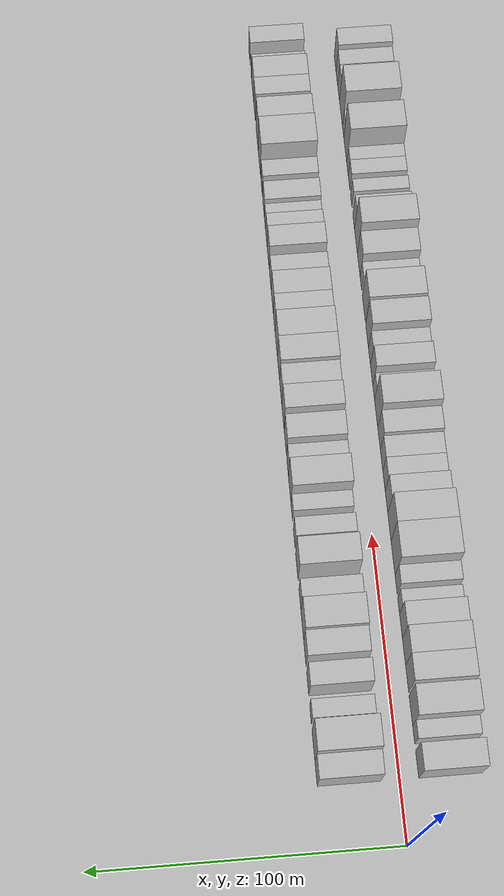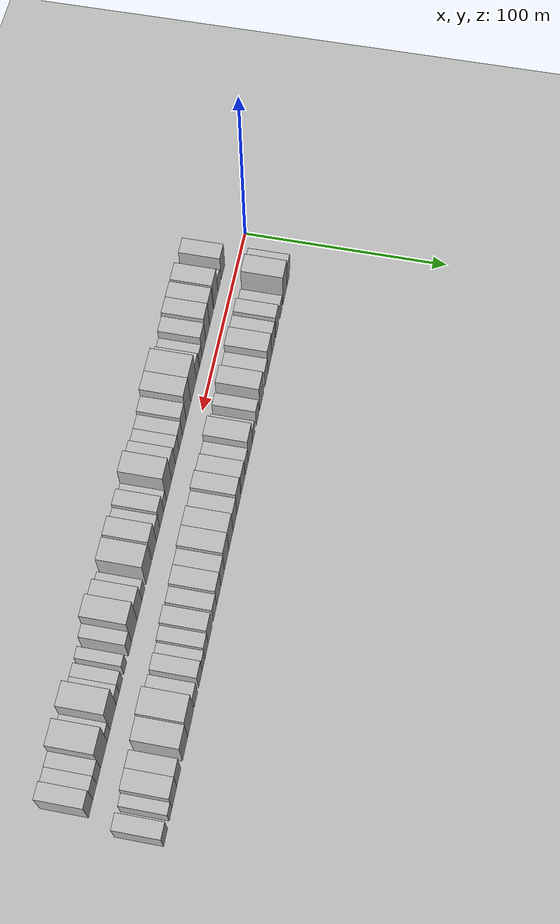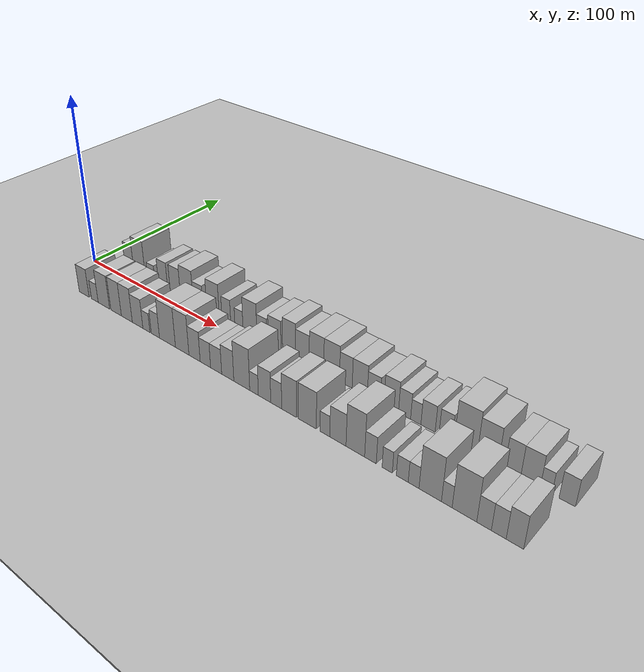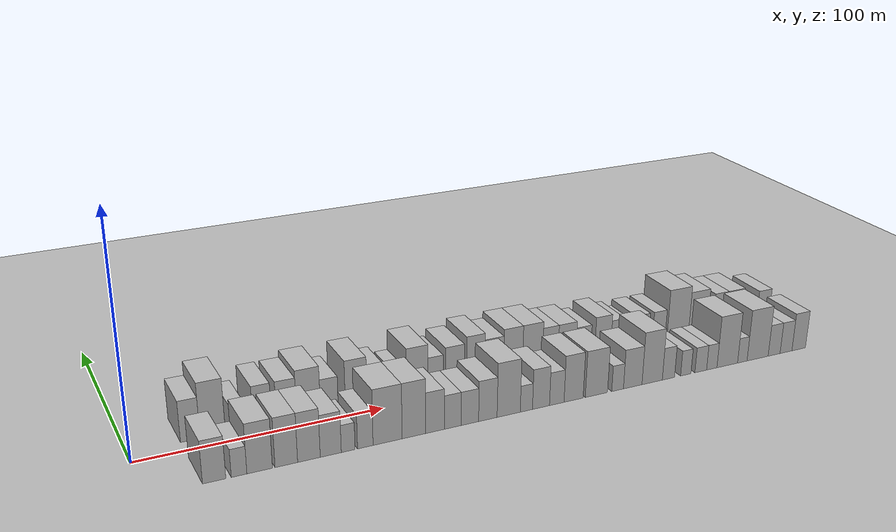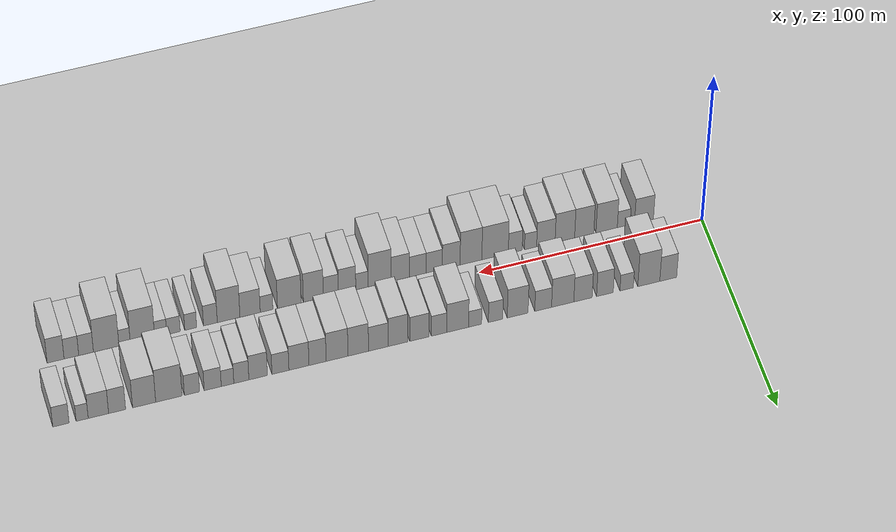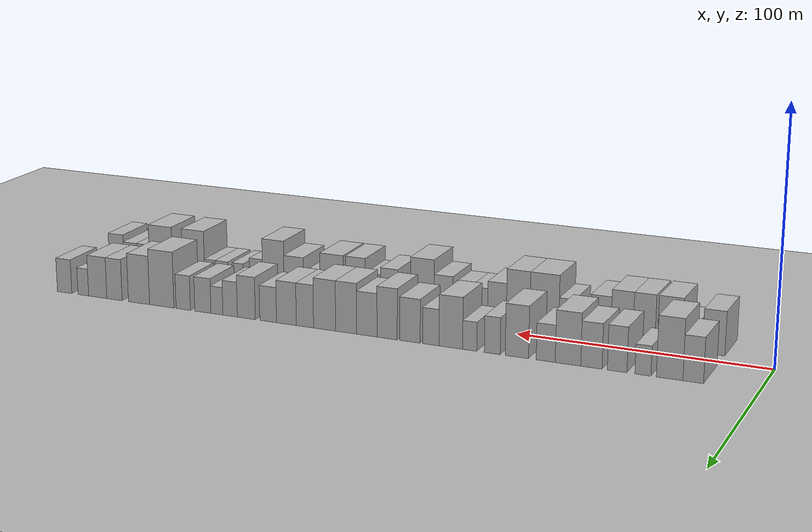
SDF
<?xml version="1.0" encoding="utf-8"?>

<sdf version="1.6">

   <world name="default">

      <gui fullscreen="0">

         <camera name="user_camera">

            <pose>-15 0 4.57585 0 0 0</pose>

            <view_controller>orbit</view_controller>

         </camera>

      </gui>

      <scene>

         <sky>

           <clouds>

             <speed>12</speed>

           </clouds>

         </sky>

         <ambient>0.4 0.4 0.4 1</ambient>

         <background>0.7 0.7 0.7 1</background>

         <shadows>1</shadows>

      </scene>

      <gravity>0 0 -9.8066</gravity>

      <magnetic_field>6e-06 2.3e-05 -4.2e-05</magnetic_field>

      <physics default="0" name="default_physics" type="ode">

         <ode>

            <solver>

               <type>quick</type>

               <iters>10</iters>

               <sor>1.0</sor>

               <use_dynamic_moi_rescaling>0</use_dynamic_moi_rescaling>

            </solver>

            <constraints>

               <cfm>0</cfm>

               <erp>0.2</erp>

               <contact_max_correcting_vel>100</contact_max_correcting_vel>

               <contact_surface_layer>0.001</contact_surface_layer>

            </constraints>

         </ode>

         <max_step_size>0.004</max_step_size>

         <real_time_factor>1</real_time_factor>

         <real_time_update_rate>250</real_time_update_rate>

      </physics>

      <light name="sun" type="directional">

         <cast_shadows>1</cast_shadows>

         <pose>0 0 10 0 0 0</pose>

         <diffuse>0.8 0.8 0.8 1</diffuse>

         <specular>0.2 0.2 0.2 1</specular>

         <attenuation>

            <range>1000</range>

            <constant>0.9</constant>

            <linear>0.01</linear>

            <quadratic>0.001</quadratic>

         </attenuation>

         <direction>-0.5 0.1 -0.9</direction>

      </light>

      <include>

         <name>ground_plane_1</name>

         <uri>model://HANNAS_ground_plane</uri>

         <pose>0 0 0  0 0 0</pose>

      </include>

      <include>

         <name>ground_plane_2</name>

         <uri>model://HANNAS_ground_plane</uri>

         <pose>100 0 0  0 0 0</pose>

      </include>

      <model name="building_1">

         <static>1</static>

         <pose frame="">23.7795 16.0000 0 0.000000 0.000000 1.570796</pose>

         <link name="link">

            <pose frame="">0 0 9.00 0 0 0</pose>

            <collision name="collision">

               <geometry>

                  <box>

                     <size>20.0000 7.5590 18.0000</size>

                  </box>

               </geometry>

               <max_contacts>10</max_contacts>

               <surface>

                  <contact>

                     <ode/>

                  </contact>

                  <bounce/>

                  <friction>

                     <torsional>

                        <ode/>

                     </torsional>

                     <ode/>

                  </friction>

               </surface>

            </collision>

            <visual name="visual">

               <cast_shadows>0</cast_shadows>

               <geometry>

                  <box>

                     <size>20.0000 7.5590 18.0000</size>

                  </box>

               </geometry>

               <material>

                  <script>

                     <uri>model://HANNAS_wall/materials/scripts</uri>

                     <uri>model://HANNAS_wall/materials/textures</uri>

                     <name>vrc/HANNAS_wall</name>

                  </script>

               </material>

            </visual>

            <self_collide>0</self_collide>

            <enable_wind>0</enable_wind>

            <kinematic>0</kinematic>

         </link>

      </model>

      <model name="building_2">

         <static>1</static>

         <pose frame="">32.4735 16.0000 0 0.000000 0.000000 1.570796</pose>

         <link name="link">

            <pose frame="">0 0 12.00 0 0 0</pose>

            <collision name="collision">

               <geometry>

                  <box>

                     <size>20.0000 9.8290 24.0000</size>

                  </box>

               </geometry>

               <max_contacts>10</max_contacts>

               <surface>

                  <contact>

                     <ode/>

                  </contact>

                  <bounce/>

                  <friction>

                     <torsional>

                        <ode/>

                     </torsional>

                     <ode/>

                  </friction>

               </surface>

            </collision>

            <visual name="visual">

               <cast_shadows>0</cast_shadows>

               <geometry>

                  <box>

                     <size>20.0000 9.8290 24.0000</size>

                  </box>

               </geometry>

               <material>

                  <script>

                     <uri>model://HANNAS_wall/materials/scripts</uri>

                     <uri>model://HANNAS_wall/materials/textures</uri>

                     <name>vrc/HANNAS_wall</name>

                  </script>

               </material>

            </visual>

            <self_collide>0</self_collide>

            <enable_wind>0</enable_wind>

            <kinematic>0</kinematic>

         </link>

      </model>

      <model name="building_3">

         <static>1</static>

         <pose frame="">42.3808 16.0000 0 0.000000 0.000000 1.570796</pose>

         <link name="link">

            <pose frame="">0 0 6.00 0 0 0</pose>

            <collision name="collision">

               <geometry>

                  <box>

                     <size>20.0000 5.9856 12.0000</size>

                  </box>

               </geometry>

               <max_contacts>10</max_contacts>

               <surface>

                  <contact>

                     <ode/>

                  </contact>

                  <bounce/>

                  <friction>

                     <torsional>

                        <ode/>

                     </torsional>

                     <ode/>

                  </friction>

               </surface>

            </collision>

            <visual name="visual">

               <cast_shadows>0</cast_shadows>

               <geometry>

                  <box>

                     <size>20.0000 5.9856 12.0000</size>

                  </box>

               </geometry>

               <material>

                  <script>

                     <uri>model://HANNAS_wall/materials/scripts</uri>

                     <uri>model://HANNAS_wall/materials/textures</uri>

                     <name>vrc/HANNAS_wall</name>

                  </script>

               </material>

            </visual>

            <self_collide>0</self_collide>

            <enable_wind>0</enable_wind>

            <kinematic>0</kinematic>

         </link>

      </model>

      <model name="building_4">

         <static>1</static>

         <pose frame="">52.0788 16.0000 0 0.000000 0.000000 1.570796</pose>

         <link name="link">

            <pose frame="">0 0 9.00 0 0 0</pose>

            <collision name="collision">

               <geometry>

                  <box>

                     <size>20.0000 7.4105 18.0000</size>

                  </box>

               </geometry>

               <max_contacts>10</max_contacts>

               <surface>

                  <contact>

                     <ode/>

                  </contact>

                  <bounce/>

                  <friction>

                     <torsional>

                        <ode/>

                     </torsional>

                     <ode/>

                  </friction>

               </surface>

            </collision>

            <visual name="visual">

               <cast_shadows>0</cast_shadows>

               <geometry>

                  <box>

                     <size>20.0000 7.4105 18.0000</size>

                  </box>

               </geometry>

               <material>

                  <script>

                     <uri>model://HANNAS_wall/materials/scripts</uri>

                     <uri>model://HANNAS_wall/materials/textures</uri>

                     <name>vrc/HANNAS_wall</name>

                  </script>

               </material>

            </visual>

            <self_collide>0</self_collide>

            <enable_wind>0</enable_wind>

            <kinematic>0</kinematic>

         </link>

      </model>

      <model name="building_5">

         <static>1</static>

         <pose frame="">61.8641 16.0000 0 0.000000 0.000000 1.570796</pose>

         <link name="link">

            <pose frame="">0 0 9.00 0 0 0</pose>

            <collision name="collision">

               <geometry>

                  <box>

                     <size>20.0000 8.1600 18.0000</size>

                  </box>

               </geometry>

               <max_contacts>10</max_contacts>

               <surface>

                  <contact>

                     <ode/>

                  </contact>

                  <bounce/>

                  <friction>

                     <torsional>

                        <ode/>

                     </torsional>

                     <ode/>

                  </friction>

               </surface>

            </collision>

            <visual name="visual">

               <cast_shadows>0</cast_shadows>

               <geometry>

                  <box>

                     <size>20.0000 8.1600 18.0000</size>

                  </box>

               </geometry>

               <material>

                  <script>

                     <uri>model://HANNAS_wall/materials/scripts</uri>

                     <uri>model://HANNAS_wall/materials/textures</uri>

                     <name>vrc/HANNAS_wall</name>

                  </script>

               </material>

            </visual>

            <self_collide>0</self_collide>

            <enable_wind>0</enable_wind>

            <kinematic>0</kinematic>

         </link>

      </model>

      <model name="building_6">

         <static>1</static>

         <pose frame="">70.8879 16.0000 0 0.000000 0.000000 1.570796</pose>

         <link name="link">

            <pose frame="">0 0 10.50 0 0 0</pose>

            <collision name="collision">

               <geometry>

                  <box>

                     <size>20.0000 9.8876 21.0000</size>

                  </box>

               </geometry>

               <max_contacts>10</max_contacts>

               <surface>

                  <contact>

                     <ode/>

                  </contact>

                  <bounce/>

                  <friction>

                     <torsional>

                        <ode/>

                     </torsional>

                     <ode/>

                  </friction>

               </surface>

            </collision>

            <visual name="visual">

               <cast_shadows>0</cast_shadows>

               <geometry>

                  <box>

                     <size>20.0000 9.8876 21.0000</size>

                  </box>

               </geometry>

               <material>

                  <script>

                     <uri>model://HANNAS_wall/materials/scripts</uri>

                     <uri>model://HANNAS_wall/materials/textures</uri>

                     <name>vrc/HANNAS_wall</name>

                  </script>

               </material>

            </visual>

            <self_collide>0</self_collide>

            <enable_wind>0</enable_wind>

            <kinematic>0</kinematic>

         </link>

      </model>

      <model name="building_7">

         <static>1</static>

         <pose frame="">79.5518 16.0000 0 0.000000 0.000000 1.570796</pose>

         <link name="link">

            <pose frame="">0 0 7.50 0 0 0</pose>

            <collision name="collision">

               <geometry>

                  <box>

                     <size>20.0000 7.4401 15.0000</size>

                  </box>

               </geometry>

               <max_contacts>10</max_contacts>

               <surface>

                  <contact>

                     <ode/>

                  </contact>

                  <bounce/>

                  <friction>

                     <torsional>

                        <ode/>

                     </torsional>

                     <ode/>

                  </friction>

               </surface>

            </collision>

            <visual name="visual">

               <cast_shadows>0</cast_shadows>

               <geometry>

                  <box>

                     <size>20.0000 7.4401 15.0000</size>

                  </box>

               </geometry>

               <material>

                  <script>

                     <uri>model://HANNAS_wall/materials/scripts</uri>

                     <uri>model://HANNAS_wall/materials/textures</uri>

                     <name>vrc/HANNAS_wall</name>

                  </script>

               </material>

            </visual>

            <self_collide>0</self_collide>

            <enable_wind>0</enable_wind>

            <kinematic>0</kinematic>

         </link>

      </model>

      <model name="building_8">

         <static>1</static>

         <pose frame="">90.8780 16.0000 0 0.000000 0.000000 1.570796</pose>

         <link name="link">

            <pose frame="">0 0 10.50 0 0 0</pose>

            <collision name="collision">

               <geometry>

                  <box>

                     <size>20.0000 9.2123 21.0000</size>

                  </box>

               </geometry>

               <max_contacts>10</max_contacts>

               <surface>

                  <contact>

                     <ode/>

                  </contact>

                  <bounce/>

                  <friction>

                     <torsional>

                        <ode/>

                     </torsional>

                     <ode/>

                  </friction>

               </surface>

            </collision>

            <visual name="visual">

               <cast_shadows>0</cast_shadows>

               <geometry>

                  <box>

                     <size>20.0000 9.2123 21.0000</size>

                  </box>

               </geometry>

               <material>

                  <script>

                     <uri>model://HANNAS_wall/materials/scripts</uri>

                     <uri>model://HANNAS_wall/materials/textures</uri>

                     <name>vrc/HANNAS_wall</name>

                  </script>

               </material>

            </visual>

            <self_collide>0</self_collide>

            <enable_wind>0</enable_wind>

            <kinematic>0</kinematic>

         </link>

      </model>

      <model name="building_9">

         <static>1</static>

         <pose frame="">100.6581 16.0000 0 0.000000 0.000000 1.570796</pose>

         <link name="link">

            <pose frame="">0 0 7.50 0 0 0</pose>

            <collision name="collision">

               <geometry>

                  <box>

                     <size>20.0000 6.3479 15.0000</size>

                  </box>

               </geometry>

               <max_contacts>10</max_contacts>

               <surface>

                  <contact>

                     <ode/>

                  </contact>

                  <bounce/>

                  <friction>

                     <torsional>

                        <ode/>

                     </torsional>

                     <ode/>

                  </friction>

               </surface>

            </collision>

            <visual name="visual">

               <cast_shadows>0</cast_shadows>

               <geometry>

                  <box>

                     <size>20.0000 6.3479 15.0000</size>

                  </box>

               </geometry>

               <material>

                  <script>

                     <uri>model://HANNAS_wall/materials/scripts</uri>

                     <uri>model://HANNAS_wall/materials/textures</uri>

                     <name>vrc/HANNAS_wall</name>

                  </script>

               </material>

            </visual>

            <self_collide>0</self_collide>

            <enable_wind>0</enable_wind>

            <kinematic>0</kinematic>

         </link>

      </model>

      <model name="building_10">

         <static>1</static>

         <pose frame="">109.7004 16.0000 0 0.000000 0.000000 1.570796</pose>

         <link name="link">

            <pose frame="">0 0 6.00 0 0 0</pose>

            <collision name="collision">

               <geometry>

                  <box>

                     <size>20.0000 5.7369 12.0000</size>

                  </box>

               </geometry>

               <max_contacts>10</max_contacts>

               <surface>

                  <contact>

                     <ode/>

                  </contact>

                  <bounce/>

                  <friction>

                     <torsional>

                        <ode/>

                     </torsional>

                     <ode/>

                  </friction>

               </surface>

            </collision>

            <visual name="visual">

               <cast_shadows>0</cast_shadows>

               <geometry>

                  <box>

                     <size>20.0000 5.7369 12.0000</size>

                  </box>

               </geometry>

               <material>

                  <script>

                     <uri>model://HANNAS_wall/materials/scripts</uri>

                     <uri>model://HANNAS_wall/materials/textures</uri>

                     <name>vrc/HANNAS_wall</name>

                  </script>

               </material>

            </visual>

            <self_collide>0</self_collide>

            <enable_wind>0</enable_wind>

            <kinematic>0</kinematic>

         </link>

      </model>

      <model name="building_11">

         <static>1</static>

         <pose frame="">117.3878 16.0000 0 0.000000 0.000000 1.570796</pose>

         <link name="link">

            <pose frame="">0 0 10.50 0 0 0</pose>

            <collision name="collision">

               <geometry>

                  <box>

                     <size>20.0000 9.6378 21.0000</size>

                  </box>

               </geometry>

               <max_contacts>10</max_contacts>

               <surface>

                  <contact>

                     <ode/>

                  </contact>

                  <bounce/>

                  <friction>

                     <torsional>

                        <ode/>

                     </torsional>

                     <ode/>

                  </friction>

               </surface>

            </collision>

            <visual name="visual">

               <cast_shadows>0</cast_shadows>

               <geometry>

                  <box>

                     <size>20.0000 9.6378 21.0000</size>

                  </box>

               </geometry>

               <material>

                  <script>

                     <uri>model://HANNAS_wall/materials/scripts</uri>

                     <uri>model://HANNAS_wall/materials/textures</uri>

                     <name>vrc/HANNAS_wall</name>

                  </script>

               </material>

            </visual>

            <self_collide>0</self_collide>

            <enable_wind>0</enable_wind>

            <kinematic>0</kinematic>

         </link>

      </model>

      <model name="building_12">

         <static>1</static>

         <pose frame="">125.5838 16.0000 0 0.000000 0.000000 1.570796</pose>

         <link name="link">

            <pose frame="">0 0 7.50 0 0 0</pose>

            <collision name="collision">

               <geometry>

                  <box>

                     <size>20.0000 6.7542 15.0000</size>

                  </box>

               </geometry>

               <max_contacts>10</max_contacts>

               <surface>

                  <contact>

                     <ode/>

                  </contact>

                  <bounce/>

                  <friction>

                     <torsional>

                        <ode/>

                     </torsional>

                     <ode/>

                  </friction>

               </surface>

            </collision>

            <visual name="visual">

               <cast_shadows>0</cast_shadows>

               <geometry>

                  <box>

                     <size>20.0000 6.7542 15.0000</size>

                  </box>

               </geometry>

               <material>

                  <script>

                     <uri>model://HANNAS_wall/materials/scripts</uri>

                     <uri>model://HANNAS_wall/materials/textures</uri>

                     <name>vrc/HANNAS_wall</name>

                  </script>

               </material>

            </visual>

            <self_collide>0</self_collide>

            <enable_wind>0</enable_wind>

            <kinematic>0</kinematic>

         </link>

      </model>

      <model name="building_13">

         <static>1</static>

         <pose frame="">134.2264 16.0000 0 0.000000 0.000000 1.570796</pose>

         <link name="link">

            <pose frame="">0 0 9.00 0 0 0</pose>

            <collision name="collision">

               <geometry>

                  <box>

                     <size>20.0000 8.5309 18.0000</size>

                  </box>

               </geometry>

               <max_contacts>10</max_contacts>

               <surface>

                  <contact>

                     <ode/>

                  </contact>

                  <bounce/>

                  <friction>

                     <torsional>

                        <ode/>

                     </torsional>

                     <ode/>

                  </friction>

               </surface>

            </collision>

            <visual name="visual">

               <cast_shadows>0</cast_shadows>

               <geometry>

                  <box>

                     <size>20.0000 8.5309 18.0000</size>

                  </box>

               </geometry>

               <material>

                  <script>

                     <uri>model://HANNAS_wall/materials/scripts</uri>

                     <uri>model://HANNAS_wall/materials/textures</uri>

                     <name>vrc/HANNAS_wall</name>

                  </script>

               </material>

            </visual>

            <self_collide>0</self_collide>

            <enable_wind>0</enable_wind>

            <kinematic>0</kinematic>

         </link>

      </model>

      <model name="building_14">

         <static>1</static>

         <pose frame="">143.7266 16.0000 0 0.000000 0.000000 1.570796</pose>

         <link name="link">

            <pose frame="">0 0 10.50 0 0 0</pose>

            <collision name="collision">

               <geometry>

                  <box>

                     <size>20.0000 8.4695 21.0000</size>

                  </box>

               </geometry>

               <max_contacts>10</max_contacts>

               <surface>

                  <contact>

                     <ode/>

                  </contact>

                  <bounce/>

                  <friction>

                     <torsional>

                        <ode/>

                     </torsional>

                     <ode/>

                  </friction>

               </surface>

            </collision>

            <visual name="visual">

               <cast_shadows>0</cast_shadows>

               <geometry>

                  <box>

                     <size>20.0000 8.4695 21.0000</size>

                  </box>

               </geometry>

               <material>

                  <script>

                     <uri>model://HANNAS_wall/materials/scripts</uri>

                     <uri>model://HANNAS_wall/materials/textures</uri>

                     <name>vrc/HANNAS_wall</name>

                  </script>

               </material>

            </visual>

            <self_collide>0</self_collide>

            <enable_wind>0</enable_wind>

            <kinematic>0</kinematic>

         </link>

      </model>

      <model name="building_15">

         <static>1</static>

         <pose frame="">152.2782 16.0000 0 0.000000 0.000000 1.570796</pose>

         <link name="link">

            <pose frame="">0 0 9.00 0 0 0</pose>

            <collision name="collision">

               <geometry>

                  <box>

                     <size>20.0000 8.6337 18.0000</size>

                  </box>

               </geometry>

               <max_contacts>10</max_contacts>

               <surface>

                  <contact>

                     <ode/>

                  </contact>

                  <bounce/>

                  <friction>

                     <torsional>

                        <ode/>

                     </torsional>

                     <ode/>

                  </friction>

               </surface>

            </collision>

            <visual name="visual">

               <cast_shadows>0</cast_shadows>

               <geometry>

                  <box>

                     <size>20.0000 8.6337 18.0000</size>

                  </box>

               </geometry>

               <material>

                  <script>

                     <uri>model://HANNAS_wall/materials/scripts</uri>

                     <uri>model://HANNAS_wall/materials/textures</uri>

                     <name>vrc/HANNAS_wall</name>

                  </script>

               </material>

            </visual>

            <self_collide>0</self_collide>

            <enable_wind>0</enable_wind>

            <kinematic>0</kinematic>

         </link>

      </model>

      <model name="building_16">

         <static>1</static>

         <pose frame="">161.0909 16.0000 0 0.000000 0.000000 1.570796</pose>

         <link name="link">

            <pose frame="">0 0 10.50 0 0 0</pose>

            <collision name="collision">

               <geometry>

                  <box>

                     <size>20.0000 8.9917 21.0000</size>

                  </box>

               </geometry>

               <max_contacts>10</max_contacts>

               <surface>

                  <contact>

                     <ode/>

                  </contact>

                  <bounce/>

                  <friction>

                     <torsional>

                        <ode/>

                     </torsional>

                     <ode/>

                  </friction>

               </surface>

            </collision>

            <visual name="visual">

               <cast_shadows>0</cast_shadows>

               <geometry>

                  <box>

                     <size>20.0000 8.9917 21.0000</size>

                  </box>

               </geometry>

               <material>

                  <script>

                     <uri>model://HANNAS_wall/materials/scripts</uri>

                     <uri>model://HANNAS_wall/materials/textures</uri>

                     <name>vrc/HANNAS_wall</name>

                  </script>

               </material>

            </visual>

            <self_collide>0</self_collide>

            <enable_wind>0</enable_wind>

            <kinematic>0</kinematic>

         </link>

      </model>

      <model name="building_17">

         <static>1</static>

         <pose frame="">170.3540 16.0000 0 0.000000 0.000000 1.570796</pose>

         <link name="link">

            <pose frame="">0 0 10.50 0 0 0</pose>

            <collision name="collision">

               <geometry>

                  <box>

                     <size>20.0000 9.5345 21.0000</size>

                  </box>

               </geometry>

               <max_contacts>10</max_contacts>

               <surface>

                  <contact>

                     <ode/>

                  </contact>

                  <bounce/>

                  <friction>

                     <torsional>

                        <ode/>

                     </torsional>

                     <ode/>

                  </friction>

               </surface>

            </collision>

            <visual name="visual">

               <cast_shadows>0</cast_shadows>

               <geometry>

                  <box>

                     <size>20.0000 9.5345 21.0000</size>

                  </box>

               </geometry>

               <material>

                  <script>

                     <uri>model://HANNAS_wall/materials/scripts</uri>

                     <uri>model://HANNAS_wall/materials/textures</uri>

                     <name>vrc/HANNAS_wall</name>

                  </script>

               </material>

            </visual>

            <self_collide>0</self_collide>

            <enable_wind>0</enable_wind>

            <kinematic>0</kinematic>

         </link>

      </model>

      <model name="building_18">

         <static>1</static>

         <pose frame="">178.8785 16.0000 0 0.000000 0.000000 1.570796</pose>

         <link name="link">

            <pose frame="">0 0 9.00 0 0 0</pose>

            <collision name="collision">

               <geometry>

                  <box>

                     <size>20.0000 7.5146 18.0000</size>

                  </box>

               </geometry>

               <max_contacts>10</max_contacts>

               <surface>

                  <contact>

                     <ode/>

                  </contact>

                  <bounce/>

                  <friction>

                     <torsional>

                        <ode/>

                     </torsional>

                     <ode/>

                  </friction>

               </surface>

            </collision>

            <visual name="visual">

               <cast_shadows>0</cast_shadows>

               <geometry>

                  <box>

                     <size>20.0000 7.5146 18.0000</size>

                  </box>

               </geometry>

               <material>

                  <script>

                     <uri>model://HANNAS_wall/materials/scripts</uri>

                     <uri>model://HANNAS_wall/materials/textures</uri>

                     <name>vrc/HANNAS_wall</name>

                  </script>

               </material>

            </visual>

            <self_collide>0</self_collide>

            <enable_wind>0</enable_wind>

            <kinematic>0</kinematic>

         </link>

      </model>

      <model name="building_19">

         <static>1</static>

         <pose frame="">187.0019 16.0000 0 0.000000 0.000000 1.570796</pose>

         <link name="link">

            <pose frame="">0 0 9.00 0 0 0</pose>

            <collision name="collision">

               <geometry>

                  <box>

                     <size>20.0000 8.7322 18.0000</size>

                  </box>

               </geometry>

               <max_contacts>10</max_contacts>

               <surface>

                  <contact>

                     <ode/>

                  </contact>

                  <bounce/>

                  <friction>

                     <torsional>

                        <ode/>

                     </torsional>

                     <ode/>

                  </friction>

               </surface>

            </collision>

            <visual name="visual">

               <cast_shadows>0</cast_shadows>

               <geometry>

                  <box>

                     <size>20.0000 8.7322 18.0000</size>

                  </box>

               </geometry>

               <material>

                  <script>

                     <uri>model://HANNAS_wall/materials/scripts</uri>

                     <uri>model://HANNAS_wall/materials/textures</uri>

                     <name>vrc/HANNAS_wall</name>

                  </script>

               </material>

            </visual>

            <self_collide>0</self_collide>

            <enable_wind>0</enable_wind>

            <kinematic>0</kinematic>

         </link>

      </model>

      <model name="building_20">

         <static>1</static>

         <pose frame="">195.0579 16.0000 0 0.000000 0.000000 1.570796</pose>

         <link name="link">

            <pose frame="">0 0 7.50 0 0 0</pose>

            <collision name="collision">

               <geometry>

                  <box>

                     <size>20.0000 7.3798 15.0000</size>

                  </box>

               </geometry>

               <max_contacts>10</max_contacts>

               <surface>

                  <contact>

                     <ode/>

                  </contact>

                  <bounce/>

                  <friction>

                     <torsional>

                        <ode/>

                     </torsional>

                     <ode/>

                  </friction>

               </surface>

            </collision>

            <visual name="visual">

               <cast_shadows>0</cast_shadows>

               <geometry>

                  <box>

                     <size>20.0000 7.3798 15.0000</size>

                  </box>

               </geometry>

               <material>

                  <script>

                     <uri>model://HANNAS_wall/materials/scripts</uri>

                     <uri>model://HANNAS_wall/materials/textures</uri>

                     <name>vrc/HANNAS_wall</name>

                  </script>

               </material>

            </visual>

            <self_collide>0</self_collide>

            <enable_wind>0</enable_wind>

            <kinematic>0</kinematic>

         </link>

      </model>

      <model name="building_21">

         <static>1</static>

         <pose frame="">204.7672 16.0000 0 0.000000 0.000000 1.570796</pose>

         <link name="link">

            <pose frame="">0 0 9.00 0 0 0</pose>

            <collision name="collision">

               <geometry>

                  <box>

                     <size>20.0000 8.0388 18.0000</size>

                  </box>

               </geometry>

               <max_contacts>10</max_contacts>

               <surface>

                  <contact>

                     <ode/>

                  </contact>

                  <bounce/>

                  <friction>

                     <torsional>

                        <ode/>

                     </torsional>

                     <ode/>

                  </friction>

               </surface>

            </collision>

            <visual name="visual">

               <cast_shadows>0</cast_shadows>

               <geometry>

                  <box>

                     <size>20.0000 8.0388 18.0000</size>

                  </box>

               </geometry>

               <material>

                  <script>

                     <uri>model://HANNAS_wall/materials/scripts</uri>

                     <uri>model://HANNAS_wall/materials/textures</uri>

                     <name>vrc/HANNAS_wall</name>

                  </script>

               </material>

            </visual>

            <self_collide>0</self_collide>

            <enable_wind>0</enable_wind>

            <kinematic>0</kinematic>

         </link>

      </model>

      <model name="building_22">

         <static>1</static>

         <pose frame="">212.0530 16.0000 0 0.000000 0.000000 1.570796</pose>

         <link name="link">

            <pose frame="">0 0 7.50 0 0 0</pose>

            <collision name="collision">

               <geometry>

                  <box>

                     <size>20.0000 6.5327 15.0000</size>

                  </box>

               </geometry>

               <max_contacts>10</max_contacts>

               <surface>

                  <contact>

                     <ode/>

                  </contact>

                  <bounce/>

                  <friction>

                     <torsional>

                        <ode/>

                     </torsional>

                     <ode/>

                  </friction>

               </surface>

            </collision>

            <visual name="visual">

               <cast_shadows>0</cast_shadows>

               <geometry>

                  <box>

                     <size>20.0000 6.5327 15.0000</size>

                  </box>

               </geometry>

               <material>

                  <script>

                     <uri>model://HANNAS_wall/materials/scripts</uri>

                     <uri>model://HANNAS_wall/materials/textures</uri>

                     <name>vrc/HANNAS_wall</name>

                  </script>

               </material>

            </visual>

            <self_collide>0</self_collide>

            <enable_wind>0</enable_wind>

            <kinematic>0</kinematic>

         </link>

      </model>

      <model name="building_23">

         <static>1</static>

         <pose frame="">218.0440 16.0000 0 0.000000 0.000000 1.570796</pose>

         <link name="link">

            <pose frame="">0 0 6.00 0 0 0</pose>

            <collision name="collision">

               <geometry>

                  <box>

                     <size>20.0000 5.4495 12.0000</size>

                  </box>

               </geometry>

               <max_contacts>10</max_contacts>

               <surface>

                  <contact>

                     <ode/>

                  </contact>

                  <bounce/>

                  <friction>

                     <torsional>

                        <ode/>

                     </torsional>

                     <ode/>

                  </friction>

               </surface>

            </collision>

            <visual name="visual">

               <cast_shadows>0</cast_shadows>

               <geometry>

                  <box>

                     <size>20.0000 5.4495 12.0000</size>

                  </box>

               </geometry>

               <material>

                  <script>

                     <uri>model://HANNAS_wall/materials/scripts</uri>

                     <uri>model://HANNAS_wall/materials/textures</uri>

                     <name>vrc/HANNAS_wall</name>

                  </script>

               </material>

            </visual>

            <self_collide>0</self_collide>

            <enable_wind>0</enable_wind>

            <kinematic>0</kinematic>

         </link>

      </model>

      <model name="building_24">

         <static>1</static>

         <pose frame="">224.4603 16.0000 0 0.000000 0.000000 1.570796</pose>

         <link name="link">

            <pose frame="">0 0 7.50 0 0 0</pose>

            <collision name="collision">

               <geometry>

                  <box>

                     <size>20.0000 7.3830 15.0000</size>

                  </box>

               </geometry>

               <max_contacts>10</max_contacts>

               <surface>

                  <contact>

                     <ode/>

                  </contact>

                  <bounce/>

                  <friction>

                     <torsional>

                        <ode/>

                     </torsional>

                     <ode/>

                  </friction>

               </surface>

            </collision>

            <visual name="visual">

               <cast_shadows>0</cast_shadows>

               <geometry>

                  <box>

                     <size>20.0000 7.3830 15.0000</size>

                  </box>

               </geometry>

               <material>

                  <script>

                     <uri>model://HANNAS_wall/materials/scripts</uri>

                     <uri>model://HANNAS_wall/materials/textures</uri>

                     <name>vrc/HANNAS_wall</name>

                  </script>

               </material>

            </visual>

            <self_collide>0</self_collide>

            <enable_wind>0</enable_wind>

            <kinematic>0</kinematic>

         </link>

      </model>

      <model name="building_25">

         <static>1</static>

         <pose frame="">233.4538 16.0000 0 0.000000 0.000000 1.570796</pose>

         <link name="link">

            <pose frame="">0 0 7.50 0 0 0</pose>

            <collision name="collision">

               <geometry>

                  <box>

                     <size>20.0000 6.6040 15.0000</size>

                  </box>

               </geometry>

               <max_contacts>10</max_contacts>

               <surface>

                  <contact>

                     <ode/>

                  </contact>

                  <bounce/>

                  <friction>

                     <torsional>

                        <ode/>

                     </torsional>

                     <ode/>

                  </friction>

               </surface>

            </collision>

            <visual name="visual">

               <cast_shadows>0</cast_shadows>

               <geometry>

                  <box>

                     <size>20.0000 6.6040 15.0000</size>

                  </box>

               </geometry>

               <material>

                  <script>

                     <uri>model://HANNAS_wall/materials/scripts</uri>

                     <uri>model://HANNAS_wall/materials/textures</uri>

                     <name>vrc/HANNAS_wall</name>

                  </script>

               </material>

            </visual>

            <self_collide>0</self_collide>

            <enable_wind>0</enable_wind>

            <kinematic>0</kinematic>

         </link>

      </model>

      <model name="building_26">

         <static>1</static>

         <pose frame="">243.4445 16.0000 0 0.000000 0.000000 1.570796</pose>

         <link name="link">

            <pose frame="">0 0 12.00 0 0 0</pose>

            <collision name="collision">

               <geometry>

                  <box>

                     <size>20.0000 11.3775 24.0000</size>

                  </box>

               </geometry>

               <max_contacts>10</max_contacts>

               <surface>

                  <contact>

                     <ode/>

                  </contact>

                  <bounce/>

                  <friction>

                     <torsional>

                        <ode/>

                     </torsional>

                     <ode/>

                  </friction>

               </surface>

            </collision>

            <visual name="visual">

               <cast_shadows>0</cast_shadows>

               <geometry>

                  <box>

                     <size>20.0000 11.3775 24.0000</size>

                  </box>

               </geometry>

               <material>

                  <script>

                     <uri>model://HANNAS_wall/materials/scripts</uri>

                     <uri>model://HANNAS_wall/materials/textures</uri>

                     <name>vrc/HANNAS_wall</name>

                  </script>

               </material>

            </visual>

            <self_collide>0</self_collide>

            <enable_wind>0</enable_wind>

            <kinematic>0</kinematic>

         </link>

      </model>

      <model name="building_27">

         <static>1</static>

         <pose frame="">254.1172 16.0000 0 0.000000 0.000000 1.570796</pose>

         <link name="link">

            <pose frame="">0 0 10.50 0 0 0</pose>

            <collision name="collision">

               <geometry>

                  <box>

                     <size>20.0000 9.9678 21.0000</size>

                  </box>

               </geometry>

               <max_contacts>10</max_contacts>

               <surface>

                  <contact>

                     <ode/>

                  </contact>

                  <bounce/>

                  <friction>

                     <torsional>

                        <ode/>

                     </torsional>

                     <ode/>

                  </friction>

               </surface>

            </collision>

            <visual name="visual">

               <cast_shadows>0</cast_shadows>

               <geometry>

                  <box>

                     <size>20.0000 9.9678 21.0000</size>

                  </box>

               </geometry>

               <material>

                  <script>

                     <uri>model://HANNAS_wall/materials/scripts</uri>

                     <uri>model://HANNAS_wall/materials/textures</uri>

                     <name>vrc/HANNAS_wall</name>

                  </script>

               </material>

            </visual>

            <self_collide>0</self_collide>

            <enable_wind>0</enable_wind>

            <kinematic>0</kinematic>

         </link>

      </model>

      <model name="building_28">

         <static>1</static>

         <pose frame="">265.7583 16.0000 0 0.000000 0.000000 1.570796</pose>

         <link name="link">

            <pose frame="">0 0 9.00 0 0 0</pose>

            <collision name="collision">

               <geometry>

                  <box>

                     <size>20.0000 7.3144 18.0000</size>

                  </box>

               </geometry>

               <max_contacts>10</max_contacts>

               <surface>

                  <contact>

                     <ode/>

                  </contact>

                  <bounce/>

                  <friction>

                     <torsional>

                        <ode/>

                     </torsional>

                     <ode/>

                  </friction>

               </surface>

            </collision>

            <visual name="visual">

               <cast_shadows>0</cast_shadows>

               <geometry>

                  <box>

                     <size>20.0000 7.3144 18.0000</size>

                  </box>

               </geometry>

               <material>

                  <script>

                     <uri>model://HANNAS_wall/materials/scripts</uri>

                     <uri>model://HANNAS_wall/materials/textures</uri>

                     <name>vrc/HANNAS_wall</name>

                  </script>

               </material>

            </visual>

            <self_collide>0</self_collide>

            <enable_wind>0</enable_wind>

            <kinematic>0</kinematic>

         </link>

      </model>

      <model name="building_29">

         <static>1</static>

         <pose frame="">273.7991 16.0000 0 0.000000 0.000000 1.570796</pose>

         <link name="link">

            <pose frame="">0 0 9.00 0 0 0</pose>

            <collision name="collision">

               <geometry>

                  <box>

                     <size>20.0000 8.7670 18.0000</size>

                  </box>

               </geometry>

               <max_contacts>10</max_contacts>

               <surface>

                  <contact>

                     <ode/>

                  </contact>

                  <bounce/>

                  <friction>

                     <torsional>

                        <ode/>

                     </torsional>

                     <ode/>

                  </friction>

               </surface>

            </collision>

            <visual name="visual">

               <cast_shadows>0</cast_shadows>

               <geometry>

                  <box>

                     <size>20.0000 8.7670 18.0000</size>

                  </box>

               </geometry>

               <material>

                  <script>

                     <uri>model://HANNAS_wall/materials/scripts</uri>

                     <uri>model://HANNAS_wall/materials/textures</uri>

                     <name>vrc/HANNAS_wall</name>

                  </script>

               </material>

            </visual>

            <self_collide>0</self_collide>

            <enable_wind>0</enable_wind>

            <kinematic>0</kinematic>

         </link>

      </model>

      <model name="building_30">

         <static>1</static>

         <pose frame="">280.7726 16.0000 0 0.000000 0.000000 1.570796</pose>

         <link name="link">

            <pose frame="">0 0 6.00 0 0 0</pose>

            <collision name="collision">

               <geometry>

                  <box>

                     <size>20.0000 5.1800 12.0000</size>

                  </box>

               </geometry>

               <max_contacts>10</max_contacts>

               <surface>

                  <contact>

                     <ode/>

                  </contact>

                  <bounce/>

                  <friction>

                     <torsional>

                        <ode/>

                     </torsional>

                     <ode/>

                  </friction>

               </surface>

            </collision>

            <visual name="visual">

               <cast_shadows>0</cast_shadows>

               <geometry>

                  <box>

                     <size>20.0000 5.1800 12.0000</size>

                  </box>

               </geometry>

               <material>

                  <script>

                     <uri>model://HANNAS_wall/materials/scripts</uri>

                     <uri>model://HANNAS_wall/materials/textures</uri>

                     <name>vrc/HANNAS_wall</name>

                  </script>

               </material>

            </visual>

            <self_collide>0</self_collide>

            <enable_wind>0</enable_wind>

            <kinematic>0</kinematic>

         </link>

      </model>

      <model name="building_31">

         <static>1</static>

         <pose frame="">289.8794 16.0000 0 0.000000 0.000000 1.570796</pose>

         <link name="link">

            <pose frame="">0 0 7.50 0 0 0</pose>

            <collision name="collision">

               <geometry>

                  <box>

                     <size>20.0000 7.0337 15.0000</size>

                  </box>

               </geometry>

               <max_contacts>10</max_contacts>

               <surface>

                  <contact>

                     <ode/>

                  </contact>

                  <bounce/>

                  <friction>

                     <torsional>

                        <ode/>

                     </torsional>

                     <ode/>

                  </friction>

               </surface>

            </collision>

            <visual name="visual">

               <cast_shadows>0</cast_shadows>

               <geometry>

                  <box>

                     <size>20.0000 7.0337 15.0000</size>

                  </box>

               </geometry>

               <material>

                  <script>

                     <uri>model://HANNAS_wall/materials/scripts</uri>

                     <uri>model://HANNAS_wall/materials/textures</uri>

                     <name>vrc/HANNAS_wall</name>

                  </script>

               </material>

            </visual>

            <self_collide>0</self_collide>

            <enable_wind>0</enable_wind>

            <kinematic>0</kinematic>

         </link>

      </model>

      <model name="building_32">

         <static>1</static>

         <pose frame="">24.2722 -16.0000 0 0.000000 0.000000 1.570796</pose>

         <link name="link">

            <pose frame="">0 0 9.00 0 0 0</pose>

            <collision name="collision">

               <geometry>

                  <box>

                     <size>20.0000 8.5445 18.0000</size>

                  </box>

               </geometry>

               <max_contacts>10</max_contacts>

               <surface>

                  <contact>

                     <ode/>

                  </contact>

                  <bounce/>

                  <friction>

                     <torsional>

                        <ode/>

                     </torsional>

                     <ode/>

                  </friction>

               </surface>

            </collision>

            <visual name="visual">

               <cast_shadows>0</cast_shadows>

               <geometry>

                  <box>

                     <size>20.0000 8.5445 18.0000</size>

                  </box>

               </geometry>

               <material>

                  <script>

                     <uri>model://HANNAS_wall/materials/scripts</uri>

                     <uri>model://HANNAS_wall/materials/textures</uri>

                     <name>vrc/HANNAS_wall</name>

                  </script>

               </material>

            </visual>

            <self_collide>0</self_collide>

            <enable_wind>0</enable_wind>

            <kinematic>0</kinematic>

         </link>

      </model>

      <model name="building_33">

         <static>1</static>

         <pose frame="">33.4394 -16.0000 0 0.000000 0.000000 1.570796</pose>

         <link name="link">

            <pose frame="">0 0 6.00 0 0 0</pose>

            <collision name="collision">

               <geometry>

                  <box>

                     <size>20.0000 5.7899 12.0000</size>

                  </box>

               </geometry>

               <max_contacts>10</max_contacts>

               <surface>

                  <contact>

                     <ode/>

                  </contact>

                  <bounce/>

                  <friction>

                     <torsional>

                        <ode/>

                     </torsional>

                     <ode/>

                  </friction>

               </surface>

            </collision>

            <visual name="visual">

               <cast_shadows>0</cast_shadows>

               <geometry>

                  <box>

                     <size>20.0000 5.7899 12.0000</size>

                  </box>

               </geometry>

               <material>

                  <script>

                     <uri>model://HANNAS_wall/materials/scripts</uri>

                     <uri>model://HANNAS_wall/materials/textures</uri>

                     <name>vrc/HANNAS_wall</name>

                  </script>

               </material>

            </visual>

            <self_collide>0</self_collide>

            <enable_wind>0</enable_wind>

            <kinematic>0</kinematic>

         </link>

      </model>

      <model name="building_34">

         <static>1</static>

         <pose frame="">41.1250 -16.0000 0 0.000000 0.000000 1.570796</pose>

         <link name="link">

            <pose frame="">0 0 10.50 0 0 0</pose>

            <collision name="collision">

               <geometry>

                  <box>

                     <size>20.0000 9.5813 21.0000</size>

                  </box>

               </geometry>

               <max_contacts>10</max_contacts>

               <surface>

                  <contact>

                     <ode/>

                  </contact>

                  <bounce/>

                  <friction>

                     <torsional>

                        <ode/>

                     </torsional>

                     <ode/>

                  </friction>

               </surface>

            </collision>

            <visual name="visual">

               <cast_shadows>0</cast_shadows>

               <geometry>

                  <box>

                     <size>20.0000 9.5813 21.0000</size>

                  </box>

               </geometry>

               <material>

                  <script>

                     <uri>model://HANNAS_wall/materials/scripts</uri>

                     <uri>model://HANNAS_wall/materials/textures</uri>

                     <name>vrc/HANNAS_wall</name>

                  </script>

               </material>

            </visual>

            <self_collide>0</self_collide>

            <enable_wind>0</enable_wind>

            <kinematic>0</kinematic>

         </link>

      </model>

      <model name="building_35">

         <static>1</static>

         <pose frame="">51.2277 -16.0000 0 0.000000 0.000000 1.570796</pose>

         <link name="link">

            <pose frame="">0 0 10.50 0 0 0</pose>

            <collision name="collision">

               <geometry>

                  <box>

                     <size>20.0000 8.6242 21.0000</size>

                  </box>

               </geometry>

               <max_contacts>10</max_contacts>

               <surface>

                  <contact>

                     <ode/>

                  </contact>

                  <bounce/>

                  <friction>

                     <torsional>

                        <ode/>

                     </torsional>

                     <ode/>

                  </friction>

               </surface>

            </collision>

            <visual name="visual">

               <cast_shadows>0</cast_shadows>

               <geometry>

                  <box>

                     <size>20.0000 8.6242 21.0000</size>

                  </box>

               </geometry>

               <material>

                  <script>

                     <uri>model://HANNAS_wall/materials/scripts</uri>

                     <uri>model://HANNAS_wall/materials/textures</uri>

                     <name>vrc/HANNAS_wall</name>

                  </script>

               </material>

            </visual>

            <self_collide>0</self_collide>

            <enable_wind>0</enable_wind>

            <kinematic>0</kinematic>

         </link>

      </model>

      <model name="building_36">

         <static>1</static>

         <pose frame="">59.9242 -16.0000 0 0.000000 0.000000 1.570796</pose>

         <link name="link">

            <pose frame="">0 0 10.50 0 0 0</pose>

            <collision name="collision">

               <geometry>

                  <box>

                     <size>20.0000 8.7688 21.0000</size>

                  </box>

               </geometry>

               <max_contacts>10</max_contacts>

               <surface>

                  <contact>

                     <ode/>

                  </contact>

                  <bounce/>

                  <friction>

                     <torsional>

                        <ode/>

                     </torsional>

                     <ode/>

                  </friction>

               </surface>

            </collision>

            <visual name="visual">

               <cast_shadows>0</cast_shadows>

               <geometry>

                  <box>

                     <size>20.0000 8.7688 21.0000</size>

                  </box>

               </geometry>

               <material>

                  <script>

                     <uri>model://HANNAS_wall/materials/scripts</uri>

                     <uri>model://HANNAS_wall/materials/textures</uri>

                     <name>vrc/HANNAS_wall</name>

                  </script>

               </material>

            </visual>

            <self_collide>0</self_collide>

            <enable_wind>0</enable_wind>

            <kinematic>0</kinematic>

         </link>

      </model>

      <model name="building_37">

         <static>1</static>

         <pose frame="">68.4403 -16.0000 0 0.000000 0.000000 1.570796</pose>

         <link name="link">

            <pose frame="">0 0 9.00 0 0 0</pose>

            <collision name="collision">

               <geometry>

                  <box>

                     <size>20.0000 8.2633 18.0000</size>

                  </box>

               </geometry>

               <max_contacts>10</max_contacts>

               <surface>

                  <contact>

                     <ode/>

                  </contact>

                  <bounce/>

                  <friction>

                     <torsional>

                        <ode/>

                     </torsional>

                     <ode/>

                  </friction>

               </surface>

            </collision>

            <visual name="visual">

               <cast_shadows>0</cast_shadows>

               <geometry>

                  <box>

                     <size>20.0000 8.2633 18.0000</size>

                  </box>

               </geometry>

               <material>

                  <script>

                     <uri>model://HANNAS_wall/materials/scripts</uri>

                     <uri>model://HANNAS_wall/materials/textures</uri>

                     <name>vrc/HANNAS_wall</name>

                  </script>

               </material>

            </visual>

            <self_collide>0</self_collide>

            <enable_wind>0</enable_wind>

            <kinematic>0</kinematic>

         </link>

      </model>

      <model name="building_38">

         <static>1</static>

         <pose frame="">75.2969 -16.0000 0 0.000000 0.000000 1.570796</pose>

         <link name="link">

            <pose frame="">0 0 6.00 0 0 0</pose>

            <collision name="collision">

               <geometry>

                  <box>

                     <size>20.0000 5.4499 12.0000</size>

                  </box>

               </geometry>

               <max_contacts>10</max_contacts>

               <surface>

                  <contact>

                     <ode/>

                  </contact>

                  <bounce/>

                  <friction>

                     <torsional>

                        <ode/>

                     </torsional>

                     <ode/>

                  </friction>

               </surface>

            </collision>

            <visual name="visual">

               <cast_shadows>0</cast_shadows>

               <geometry>

                  <box>

                     <size>20.0000 5.4499 12.0000</size>

                  </box>

               </geometry>

               <material>

                  <script>

                     <uri>model://HANNAS_wall/materials/scripts</uri>

                     <uri>model://HANNAS_wall/materials/textures</uri>

                     <name>vrc/HANNAS_wall</name>

                  </script>

               </material>

            </visual>

            <self_collide>0</self_collide>

            <enable_wind>0</enable_wind>

            <kinematic>0</kinematic>

         </link>

      </model>

      <model name="building_39">

         <static>1</static>

         <pose frame="">82.1391 -16.0000 0 0.000000 0.000000 1.570796</pose>

         <link name="link">

            <pose frame="">0 0 7.50 0 0 0</pose>

            <collision name="collision">

               <geometry>

                  <box>

                     <size>20.0000 6.2345 15.0000</size>

                  </box>

               </geometry>

               <max_contacts>10</max_contacts>

               <surface>

                  <contact>

                     <ode/>

                  </contact>

                  <bounce/>

                  <friction>

                     <torsional>

                        <ode/>

                     </torsional>

                     <ode/>

                  </friction>

               </surface>

            </collision>

            <visual name="visual">

               <cast_shadows>0</cast_shadows>

               <geometry>

                  <box>

                     <size>20.0000 6.2345 15.0000</size>

                  </box>

               </geometry>

               <material>

                  <script>

                     <uri>model://HANNAS_wall/materials/scripts</uri>

                     <uri>model://HANNAS_wall/materials/textures</uri>

                     <name>vrc/HANNAS_wall</name>

                  </script>

               </material>

            </visual>

            <self_collide>0</self_collide>

            <enable_wind>0</enable_wind>

            <kinematic>0</kinematic>

         </link>

      </model>

      <model name="building_40">

         <static>1</static>

         <pose frame="">91.1727 -16.0000 0 0.000000 0.000000 1.570796</pose>

         <link name="link">

            <pose frame="">0 0 12.00 0 0 0</pose>

            <collision name="collision">

               <geometry>

                  <box>

                     <size>20.0000 11.8327 24.0000</size>

                  </box>

               </geometry>

               <max_contacts>10</max_contacts>

               <surface>

                  <contact>

                     <ode/>

                  </contact>

                  <bounce/>

                  <friction>

                     <torsional>

                        <ode/>

                     </torsional>

                     <ode/>

                  </friction>

               </surface>

            </collision>

            <visual name="visual">

               <cast_shadows>0</cast_shadows>

               <geometry>

                  <box>

                     <size>20.0000 11.8327 24.0000</size>

                  </box>

               </geometry>

               <material>

                  <script>

                     <uri>model://HANNAS_wall/materials/scripts</uri>

                     <uri>model://HANNAS_wall/materials/textures</uri>

                     <name>vrc/HANNAS_wall</name>

                  </script>

               </material>

            </visual>

            <self_collide>0</self_collide>

            <enable_wind>0</enable_wind>

            <kinematic>0</kinematic>

         </link>

      </model>

      <model name="building_41">

         <static>1</static>

         <pose frame="">101.9414 -16.0000 0 0.000000 0.000000 1.570796</pose>

         <link name="link">

            <pose frame="">0 0 12.00 0 0 0</pose>

            <collision name="collision">

               <geometry>

                  <box>

                     <size>20.0000 9.7045 24.0000</size>

                  </box>

               </geometry>

               <max_contacts>10</max_contacts>

               <surface>

                  <contact>

                     <ode/>

                  </contact>

                  <bounce/>

                  <friction>

                     <torsional>

                        <ode/>

                     </torsional>

                     <ode/>

                  </friction>

               </surface>

            </collision>

            <visual name="visual">

               <cast_shadows>0</cast_shadows>

               <geometry>

                  <box>

                     <size>20.0000 9.7045 24.0000</size>

                  </box>

               </geometry>

               <material>

                  <script>

                     <uri>model://HANNAS_wall/materials/scripts</uri>

                     <uri>model://HANNAS_wall/materials/textures</uri>

                     <name>vrc/HANNAS_wall</name>

                  </script>

               </material>

            </visual>

            <self_collide>0</self_collide>

            <enable_wind>0</enable_wind>

            <kinematic>0</kinematic>

         </link>

      </model>

      <model name="building_42">

         <static>1</static>

         <pose frame="">110.7455 -16.0000 0 0.000000 0.000000 1.570796</pose>

         <link name="link">

            <pose frame="">0 0 9.00 0 0 0</pose>

            <collision name="collision">

               <geometry>

                  <box>

                     <size>20.0000 7.9038 18.0000</size>

                  </box>

               </geometry>

               <max_contacts>10</max_contacts>

               <surface>

                  <contact>

                     <ode/>

                  </contact>

                  <bounce/>

                  <friction>

                     <torsional>

                        <ode/>

                     </torsional>

                     <ode/>

                  </friction>

               </surface>

            </collision>

            <visual name="visual">

               <cast_shadows>0</cast_shadows>

               <geometry>

                  <box>

                     <size>20.0000 7.9038 18.0000</size>

                  </box>

               </geometry>

               <material>

                  <script>

                     <uri>model://HANNAS_wall/materials/scripts</uri>

                     <uri>model://HANNAS_wall/materials/textures</uri>

                     <name>vrc/HANNAS_wall</name>

                  </script>

               </material>

            </visual>

            <self_collide>0</self_collide>

            <enable_wind>0</enable_wind>

            <kinematic>0</kinematic>

         </link>

      </model>

      <model name="building_43">

         <static>1</static>

         <pose frame="">118.2795 -16.0000 0 0.000000 0.000000 1.570796</pose>

         <link name="link">

            <pose frame="">0 0 7.50 0 0 0</pose>

            <collision name="collision">

               <geometry>

                  <box>

                     <size>20.0000 7.1643 15.0000</size>

                  </box>

               </geometry>

               <max_contacts>10</max_contacts>

               <surface>

                  <contact>

                     <ode/>

                  </contact>

                  <bounce/>

                  <friction>

                     <torsional>

                        <ode/>

                     </torsional>

                     <ode/>

                  </friction>

               </surface>

            </collision>

            <visual name="visual">

               <cast_shadows>0</cast_shadows>

               <geometry>

                  <box>

                     <size>20.0000 7.1643 15.0000</size>

                  </box>

               </geometry>

               <material>

                  <script>

                     <uri>model://HANNAS_wall/materials/scripts</uri>

                     <uri>model://HANNAS_wall/materials/textures</uri>

                     <name>vrc/HANNAS_wall</name>

                  </script>

               </material>

            </visual>

            <self_collide>0</self_collide>

            <enable_wind>0</enable_wind>

            <kinematic>0</kinematic>

         </link>

      </model>

      <model name="building_44">

         <static>1</static>

         <pose frame="">125.6109 -16.0000 0 0.000000 0.000000 1.570796</pose>

         <link name="link">

            <pose frame="">0 0 7.50 0 0 0</pose>

            <collision name="collision">

               <geometry>

                  <box>

                     <size>20.0000 7.4984 15.0000</size>

                  </box>

               </geometry>

               <max_contacts>10</max_contacts>

               <surface>

                  <contact>

                     <ode/>

                  </contact>

                  <bounce/>

                  <friction>

                     <torsional>

                        <ode/>

                     </torsional>

                     <ode/>

                  </friction>

               </surface>

            </collision>

            <visual name="visual">

               <cast_shadows>0</cast_shadows>

               <geometry>

                  <box>

                     <size>20.0000 7.4984 15.0000</size>

                  </box>

               </geometry>

               <material>

                  <script>

                     <uri>model://HANNAS_wall/materials/scripts</uri>

                     <uri>model://HANNAS_wall/materials/textures</uri>

                     <name>vrc/HANNAS_wall</name>

                  </script>

               </material>

            </visual>

            <self_collide>0</self_collide>

            <enable_wind>0</enable_wind>

            <kinematic>0</kinematic>

         </link>

      </model>

      <model name="building_45">

         <static>1</static>

         <pose frame="">133.3753 -16.0000 0 0.000000 0.000000 1.570796</pose>

         <link name="link">

            <pose frame="">0 0 9.00 0 0 0</pose>

            <collision name="collision">

               <geometry>

                  <box>

                     <size>20.0000 8.0305 18.0000</size>

                  </box>

               </geometry>

               <max_contacts>10</max_contacts>

               <surface>

                  <contact>

                     <ode/>

                  </contact>

                  <bounce/>

                  <friction>

                     <torsional>

                        <ode/>

                     </torsional>

                     <ode/>

                  </friction>

               </surface>

            </collision>

            <visual name="visual">

               <cast_shadows>0</cast_shadows>

               <geometry>

                  <box>

                     <size>20.0000 8.0305 18.0000</size>

                  </box>

               </geometry>

               <material>

                  <script>

                     <uri>model://HANNAS_wall/materials/scripts</uri>

                     <uri>model://HANNAS_wall/materials/textures</uri>

                     <name>vrc/HANNAS_wall</name>

                  </script>

               </material>

            </visual>

            <self_collide>0</self_collide>

            <enable_wind>0</enable_wind>

            <kinematic>0</kinematic>

         </link>

      </model>

      <model name="building_46">

         <static>1</static>

         <pose frame="">142.5112 -16.0000 0 0.000000 0.000000 1.570796</pose>

         <link name="link">

            <pose frame="">0 0 12.00 0 0 0</pose>

            <collision name="collision">

               <geometry>

                  <box>

                     <size>20.0000 10.2413 24.0000</size>

                  </box>

               </geometry>

               <max_contacts>10</max_contacts>

               <surface>

                  <contact>

                     <ode/>

                  </contact>

                  <bounce/>

                  <friction>

                     <torsional>

                        <ode/>

                     </torsional>

                     <ode/>

                  </friction>

               </surface>

            </collision>

            <visual name="visual">

               <cast_shadows>0</cast_shadows>

               <geometry>

                  <box>

                     <size>20.0000 10.2413 24.0000</size>

                  </box>

               </geometry>

               <material>

                  <script>

                     <uri>model://HANNAS_wall/materials/scripts</uri>

                     <uri>model://HANNAS_wall/materials/textures</uri>

                     <name>vrc/HANNAS_wall</name>

                  </script>

               </material>

            </visual>

            <self_collide>0</self_collide>

            <enable_wind>0</enable_wind>

            <kinematic>0</kinematic>

         </link>

      </model>

      <model name="building_47">

         <static>1</static>

         <pose frame="">150.3586 -16.0000 0 0.000000 0.000000 1.570796</pose>

         <link name="link">

            <pose frame="">0 0 6.00 0 0 0</pose>

            <collision name="collision">

               <geometry>

                  <box>

                     <size>20.0000 5.4535 12.0000</size>

                  </box>

               </geometry>

               <max_contacts>10</max_contacts>

               <surface>

                  <contact>

                     <ode/>

                  </contact>

                  <bounce/>

                  <friction>

                     <torsional>

                        <ode/>

                     </torsional>

                     <ode/>

                  </friction>

               </surface>

            </collision>

            <visual name="visual">

               <cast_shadows>0</cast_shadows>

               <geometry>

                  <box>

                     <size>20.0000 5.4535 12.0000</size>

                  </box>

               </geometry>

               <material>

                  <script>

                     <uri>model://HANNAS_wall/materials/scripts</uri>

                     <uri>model://HANNAS_wall/materials/textures</uri>

                     <name>vrc/HANNAS_wall</name>

                  </script>

               </material>

            </visual>

            <self_collide>0</self_collide>

            <enable_wind>0</enable_wind>

            <kinematic>0</kinematic>

         </link>

      </model>

      <model name="building_48">

         <static>1</static>

         <pose frame="">156.9252 -16.0000 0 0.000000 0.000000 1.570796</pose>

         <link name="link">

            <pose frame="">0 0 9.00 0 0 0</pose>

            <collision name="collision">

               <geometry>

                  <box>

                     <size>20.0000 7.6798 18.0000</size>

                  </box>

               </geometry>

               <max_contacts>10</max_contacts>

               <surface>

                  <contact>

                     <ode/>

                  </contact>

                  <bounce/>

                  <friction>

                     <torsional>

                        <ode/>

                     </torsional>

                     <ode/>

                  </friction>

               </surface>

            </collision>

            <visual name="visual">

               <cast_shadows>0</cast_shadows>

               <geometry>

                  <box>

                     <size>20.0000 7.6798 18.0000</size>

                  </box>

               </geometry>

               <material>

                  <script>

                     <uri>model://HANNAS_wall/materials/scripts</uri>

                     <uri>model://HANNAS_wall/materials/textures</uri>

                     <name>vrc/HANNAS_wall</name>

                  </script>

               </material>

            </visual>

            <self_collide>0</self_collide>

            <enable_wind>0</enable_wind>

            <kinematic>0</kinematic>

         </link>

      </model>

      <model name="building_49">

         <static>1</static>

         <pose frame="">164.0865 -16.0000 0 0.000000 0.000000 1.570796</pose>

         <link name="link">

            <pose frame="">0 0 7.50 0 0 0</pose>

            <collision name="collision">

               <geometry>

                  <box>

                     <size>20.0000 6.6427 15.0000</size>

                  </box>

               </geometry>

               <max_contacts>10</max_contacts>

               <surface>

                  <contact>

                     <ode/>

                  </contact>

                  <bounce/>

                  <friction>

                     <torsional>

                        <ode/>

                     </torsional>

                     <ode/>

                  </friction>

               </surface>

            </collision>

            <visual name="visual">

               <cast_shadows>0</cast_shadows>

               <geometry>

                  <box>

                     <size>20.0000 6.6427 15.0000</size>

                  </box>

               </geometry>

               <material>

                  <script>

                     <uri>model://HANNAS_wall/materials/scripts</uri>

                     <uri>model://HANNAS_wall/materials/textures</uri>

                     <name>vrc/HANNAS_wall</name>

                  </script>

               </material>

            </visual>

            <self_collide>0</self_collide>

            <enable_wind>0</enable_wind>

            <kinematic>0</kinematic>

         </link>

      </model>

      <model name="building_50">

         <static>1</static>

         <pose frame="">171.8131 -16.0000 0 0.000000 0.000000 1.570796</pose>

         <link name="link">

            <pose frame="">0 0 10.50 0 0 0</pose>

            <collision name="collision">

               <geometry>

                  <box>

                     <size>20.0000 8.8105 21.0000</size>

                  </box>

               </geometry>

               <max_contacts>10</max_contacts>

               <surface>

                  <contact>

                     <ode/>

                  </contact>

                  <bounce/>

                  <friction>

                     <torsional>

                        <ode/>

                     </torsional>

                     <ode/>

                  </friction>

               </surface>

            </collision>

            <visual name="visual">

               <cast_shadows>0</cast_shadows>

               <geometry>

                  <box>

                     <size>20.0000 8.8105 21.0000</size>

                  </box>

               </geometry>

               <material>

                  <script>

                     <uri>model://HANNAS_wall/materials/scripts</uri>

                     <uri>model://HANNAS_wall/materials/textures</uri>

                     <name>vrc/HANNAS_wall</name>

                  </script>

               </material>

            </visual>

            <self_collide>0</self_collide>

            <enable_wind>0</enable_wind>

            <kinematic>0</kinematic>

         </link>

      </model>

      <model name="building_51">

         <static>1</static>

         <pose frame="">182.4260 -16.0000 0 0.000000 0.000000 1.570796</pose>

         <link name="link">

            <pose frame="">0 0 10.50 0 0 0</pose>

            <collision name="collision">

               <geometry>

                  <box>

                     <size>20.0000 10.4154 21.0000</size>

                  </box>

               </geometry>

               <max_contacts>10</max_contacts>

               <surface>

                  <contact>

                     <ode/>

                  </contact>

                  <bounce/>

                  <friction>

                     <torsional>

                        <ode/>

                     </torsional>

                     <ode/>

                  </friction>

               </surface>

            </collision>

            <visual name="visual">

               <cast_shadows>0</cast_shadows>

               <geometry>

                  <box>

                     <size>20.0000 10.4154 21.0000</size>

                  </box>

               </geometry>

               <material>

                  <script>

                     <uri>model://HANNAS_wall/materials/scripts</uri>

                     <uri>model://HANNAS_wall/materials/textures</uri>

                     <name>vrc/HANNAS_wall</name>

                  </script>

               </material>

            </visual>

            <self_collide>0</self_collide>

            <enable_wind>0</enable_wind>

            <kinematic>0</kinematic>

         </link>

      </model>

      <model name="building_52">

         <static>1</static>

         <pose frame="">192.4136 -16.0000 0 0.000000 0.000000 1.570796</pose>

         <link name="link">

            <pose frame="">0 0 6.00 0 0 0</pose>

            <collision name="collision">

               <geometry>

                  <box>

                     <size>20.0000 5.5596 12.0000</size>

                  </box>

               </geometry>

               <max_contacts>10</max_contacts>

               <surface>

                  <contact>

                     <ode/>

                  </contact>

                  <bounce/>

                  <friction>

                     <torsional>

                        <ode/>

                     </torsional>

                     <ode/>

                  </friction>

               </surface>

            </collision>

            <visual name="visual">

               <cast_shadows>0</cast_shadows>

               <geometry>

                  <box>

                     <size>20.0000 5.5596 12.0000</size>

                  </box>

               </geometry>

               <material>

                  <script>

                     <uri>model://HANNAS_wall/materials/scripts</uri>

                     <uri>model://HANNAS_wall/materials/textures</uri>

                     <name>vrc/HANNAS_wall</name>

                  </script>

               </material>

            </visual>

            <self_collide>0</self_collide>

            <enable_wind>0</enable_wind>

            <kinematic>0</kinematic>

         </link>

      </model>

      <model name="building_53">

         <static>1</static>

         <pose frame="">199.6491 -16.0000 0 0.000000 0.000000 1.570796</pose>

         <link name="link">

            <pose frame="">0 0 9.00 0 0 0</pose>

            <collision name="collision">

               <geometry>

                  <box>

                     <size>20.0000 8.9115 18.0000</size>

                  </box>

               </geometry>

               <max_contacts>10</max_contacts>

               <surface>

                  <contact>

                     <ode/>

                  </contact>

                  <bounce/>

                  <friction>

                     <torsional>

                        <ode/>

                     </torsional>

                     <ode/>

                  </friction>

               </surface>

            </collision>

            <visual name="visual">

               <cast_shadows>0</cast_shadows>

               <geometry>

                  <box>

                     <size>20.0000 8.9115 18.0000</size>

                  </box>

               </geometry>

               <material>

                  <script>

                     <uri>model://HANNAS_wall/materials/scripts</uri>

                     <uri>model://HANNAS_wall/materials/textures</uri>

                     <name>vrc/HANNAS_wall</name>

                  </script>

               </material>

            </visual>

            <self_collide>0</self_collide>

            <enable_wind>0</enable_wind>

            <kinematic>0</kinematic>

         </link>

      </model>

      <model name="building_54">

         <static>1</static>

         <pose frame="">209.0632 -16.0000 0 0.000000 0.000000 1.570796</pose>

         <link name="link">

            <pose frame="">0 0 12.00 0 0 0</pose>

            <collision name="collision">

               <geometry>

                  <box>

                     <size>20.0000 9.9168 24.0000</size>

                  </box>

               </geometry>

               <max_contacts>10</max_contacts>

               <surface>

                  <contact>

                     <ode/>

                  </contact>

                  <bounce/>

                  <friction>

                     <torsional>

                        <ode/>

                     </torsional>

                     <ode/>

                  </friction>

               </surface>

            </collision>

            <visual name="visual">

               <cast_shadows>0</cast_shadows>

               <geometry>

                  <box>

                     <size>20.0000 9.9168 24.0000</size>

                  </box>

               </geometry>

               <material>

                  <script>

                     <uri>model://HANNAS_wall/materials/scripts</uri>

                     <uri>model://HANNAS_wall/materials/textures</uri>

                     <name>vrc/HANNAS_wall</name>

                  </script>

               </material>

            </visual>

            <self_collide>0</self_collide>

            <enable_wind>0</enable_wind>

            <kinematic>0</kinematic>

         </link>

      </model>

      <model name="building_55">

         <static>1</static>

         <pose frame="">217.0386 -16.0000 0 0.000000 0.000000 1.570796</pose>

         <link name="link">

            <pose frame="">0 0 7.50 0 0 0</pose>

            <collision name="collision">

               <geometry>

                  <box>

                     <size>20.0000 6.0341 15.0000</size>

                  </box>

               </geometry>

               <max_contacts>10</max_contacts>

               <surface>

                  <contact>

                     <ode/>

                  </contact>

                  <bounce/>

                  <friction>

                     <torsional>

                        <ode/>

                     </torsional>

                     <ode/>

                  </friction>

               </surface>

            </collision>

            <visual name="visual">

               <cast_shadows>0</cast_shadows>

               <geometry>

                  <box>

                     <size>20.0000 6.0341 15.0000</size>

                  </box>

               </geometry>

               <material>

                  <script>

                     <uri>model://HANNAS_wall/materials/scripts</uri>

                     <uri>model://HANNAS_wall/materials/textures</uri>

                     <name>vrc/HANNAS_wall</name>

                  </script>

               </material>

            </visual>

            <self_collide>0</self_collide>

            <enable_wind>0</enable_wind>

            <kinematic>0</kinematic>

         </link>

      </model>

      <model name="building_56">

         <static>1</static>

         <pose frame="">225.6413 -16.0000 0 0.000000 0.000000 1.570796</pose>

         <link name="link">

            <pose frame="">0 0 6.00 0 0 0</pose>

            <collision name="collision">

               <geometry>

                  <box>

                     <size>20.0000 5.1713 12.0000</size>

                  </box>

               </geometry>

               <max_contacts>10</max_contacts>

               <surface>

                  <contact>

                     <ode/>

                  </contact>

                  <bounce/>

                  <friction>

                     <torsional>

                        <ode/>

                     </torsional>

                     <ode/>

                  </friction>

               </surface>

            </collision>

            <visual name="visual">

               <cast_shadows>0</cast_shadows>

               <geometry>

                  <box>

                     <size>20.0000 5.1713 12.0000</size>

                  </box>

               </geometry>

               <material>

                  <script>

                     <uri>model://HANNAS_wall/materials/scripts</uri>

                     <uri>model://HANNAS_wall/materials/textures</uri>

                     <name>vrc/HANNAS_wall</name>

                  </script>

               </material>

            </visual>

            <self_collide>0</self_collide>

            <enable_wind>0</enable_wind>

            <kinematic>0</kinematic>

         </link>

      </model>

      <model name="building_57">

         <static>1</static>

         <pose frame="">233.1741 -16.0000 0 0.000000 0.000000 1.570796</pose>

         <link name="link">

            <pose frame="">0 0 6.00 0 0 0</pose>

            <collision name="collision">

               <geometry>

                  <box>

                     <size>20.0000 5.8944 12.0000</size>

                  </box>

               </geometry>

               <max_contacts>10</max_contacts>

               <surface>

                  <contact>

                     <ode/>

                  </contact>

                  <bounce/>

                  <friction>

                     <torsional>

                        <ode/>

                     </torsional>

                     <ode/>

                  </friction>

               </surface>

            </collision>

            <visual name="visual">

               <cast_shadows>0</cast_shadows>

               <geometry>

                  <box>

                     <size>20.0000 5.8944 12.0000</size>

                  </box>

               </geometry>

               <material>

                  <script>

                     <uri>model://HANNAS_wall/materials/scripts</uri>

                     <uri>model://HANNAS_wall/materials/textures</uri>

                     <name>vrc/HANNAS_wall</name>

                  </script>

               </material>

            </visual>

            <self_collide>0</self_collide>

            <enable_wind>0</enable_wind>

            <kinematic>0</kinematic>

         </link>

      </model>

      <model name="building_58">

         <static>1</static>

         <pose frame="">238.7428 -16.0000 0 0.000000 0.000000 1.570796</pose>

         <link name="link">

            <pose frame="">0 0 6.00 0 0 0</pose>

            <collision name="collision">

               <geometry>

                  <box>

                     <size>20.0000 5.2430 12.0000</size>

                  </box>

               </geometry>

               <max_contacts>10</max_contacts>

               <surface>

                  <contact>

                     <ode/>

                  </contact>

                  <bounce/>

                  <friction>

                     <torsional>

                        <ode/>

                     </torsional>

                     <ode/>

                  </friction>

               </surface>

            </collision>

            <visual name="visual">

               <cast_shadows>0</cast_shadows>

               <geometry>

                  <box>

                     <size>20.0000 5.2430 12.0000</size>

                  </box>

               </geometry>

               <material>

                  <script>

                     <uri>model://HANNAS_wall/materials/scripts</uri>

                     <uri>model://HANNAS_wall/materials/textures</uri>

                     <name>vrc/HANNAS_wall</name>

                  </script>

               </material>

            </visual>

            <self_collide>0</self_collide>

            <enable_wind>0</enable_wind>

            <kinematic>0</kinematic>

         </link>

      </model>

      <model name="building_59">

         <static>1</static>

         <pose frame="">246.6703 -16.0000 0 0.000000 0.000000 1.570796</pose>

         <link name="link">

            <pose frame="">0 0 12.00 0 0 0</pose>

            <collision name="collision">

               <geometry>

                  <box>

                     <size>20.0000 10.6120 24.0000</size>

                  </box>

               </geometry>

               <max_contacts>10</max_contacts>

               <surface>

                  <contact>

                     <ode/>

                  </contact>

                  <bounce/>

                  <friction>

                     <torsional>

                        <ode/>

                     </torsional>

                     <ode/>

                  </friction>

               </surface>

            </collision>

            <visual name="visual">

               <cast_shadows>0</cast_shadows>

               <geometry>

                  <box>

                     <size>20.0000 10.6120 24.0000</size>

                  </box>

               </geometry>

               <material>

                  <script>

                     <uri>model://HANNAS_wall/materials/scripts</uri>

                     <uri>model://HANNAS_wall/materials/textures</uri>

                     <name>vrc/HANNAS_wall</name>

                  </script>

               </material>

            </visual>

            <self_collide>0</self_collide>

            <enable_wind>0</enable_wind>

            <kinematic>0</kinematic>

         </link>

      </model>

      <model name="building_60">

         <static>1</static>

         <pose frame="">254.4450 -16.0000 0 0.000000 0.000000 1.570796</pose>

         <link name="link">

            <pose frame="">0 0 6.00 0 0 0</pose>

            <collision name="collision">

               <geometry>

                  <box>

                     <size>20.0000 4.9373 12.0000</size>

                  </box>

               </geometry>

               <max_contacts>10</max_contacts>

               <surface>

                  <contact>

                     <ode/>

                  </contact>

                  <bounce/>

                  <friction>

                     <torsional>

                        <ode/>

                     </torsional>

                     <ode/>

                  </friction>

               </surface>

            </collision>

            <visual name="visual">

               <cast_shadows>0</cast_shadows>

               <geometry>

                  <box>

                     <size>20.0000 4.9373 12.0000</size>

                  </box>

               </geometry>

               <material>

                  <script>

                     <uri>model://HANNAS_wall/materials/scripts</uri>

                     <uri>model://HANNAS_wall/materials/textures</uri>

                     <name>vrc/HANNAS_wall</name>

                  </script>

               </material>

            </visual>

            <self_collide>0</self_collide>

            <enable_wind>0</enable_wind>

            <kinematic>0</kinematic>

         </link>

      </model>

      <model name="building_61">

         <static>1</static>

         <pose frame="">262.4564 -16.0000 0 0.000000 0.000000 1.570796</pose>

         <link name="link">

            <pose frame="">0 0 12.00 0 0 0</pose>

            <collision name="collision">

               <geometry>

                  <box>

                     <size>20.0000 11.0855 24.0000</size>

                  </box>

               </geometry>

               <max_contacts>10</max_contacts>

               <surface>

                  <contact>

                     <ode/>

                  </contact>

                  <bounce/>

                  <friction>

                     <torsional>

                        <ode/>

                     </torsional>

                     <ode/>

                  </friction>

               </surface>

            </collision>

            <visual name="visual">

               <cast_shadows>0</cast_shadows>

               <geometry>

                  <box>

                     <size>20.0000 11.0855 24.0000</size>

                  </box>

               </geometry>

               <material>

                  <script>

                     <uri>model://HANNAS_wall/materials/scripts</uri>

                     <uri>model://HANNAS_wall/materials/textures</uri>

                     <name>vrc/HANNAS_wall</name>

                  </script>

               </material>

            </visual>

            <self_collide>0</self_collide>

            <enable_wind>0</enable_wind>

            <kinematic>0</kinematic>

         </link>

      </model>

      <model name="building_62">

         <static>1</static>

         <pose frame="">271.1821 -16.0000 0 0.000000 0.000000 1.570796</pose>

         <link name="link">

            <pose frame="">0 0 7.50 0 0 0</pose>

            <collision name="collision">

               <geometry>

                  <box>

                     <size>20.0000 6.3659 15.0000</size>

                  </box>

               </geometry>

               <max_contacts>10</max_contacts>

               <surface>

                  <contact>

                     <ode/>

                  </contact>

                  <bounce/>

                  <friction>

                     <torsional>

                        <ode/>

                     </torsional>

                     <ode/>

                  </friction>

               </surface>

            </collision>

            <visual name="visual">

               <cast_shadows>0</cast_shadows>

               <geometry>

                  <box>

                     <size>20.0000 6.3659 15.0000</size>

                  </box>

               </geometry>

               <material>

                  <script>

                     <uri>model://HANNAS_wall/materials/scripts</uri>

                     <uri>model://HANNAS_wall/materials/textures</uri>

                     <name>vrc/HANNAS_wall</name>

                  </script>

               </material>

            </visual>

            <self_collide>0</self_collide>

            <enable_wind>0</enable_wind>

            <kinematic>0</kinematic>

         </link>

      </model>

      <model name="building_63">

         <static>1</static>

         <pose frame="">277.5419 -16.0000 0 0.000000 0.000000 1.570796</pose>

         <link name="link">

            <pose frame="">0 0 7.50 0 0 0</pose>

            <collision name="collision">

               <geometry>

                  <box>

                     <size>20.0000 6.3537 15.0000</size>

                  </box>

               </geometry>

               <max_contacts>10</max_contacts>

               <surface>

                  <contact>

                     <ode/>

                  </contact>

                  <bounce/>

                  <friction>

                     <torsional>

                        <ode/>

                     </torsional>

                     <ode/>

                  </friction>

               </surface>

            </collision>

            <visual name="visual">

               <cast_shadows>0</cast_shadows>

               <geometry>

                  <box>

                     <size>20.0000 6.3537 15.0000</size>

                  </box>

               </geometry>

               <material>

                  <script>

                     <uri>model://HANNAS_wall/materials/scripts</uri>

                     <uri>model://HANNAS_wall/materials/textures</uri>

                     <name>vrc/HANNAS_wall</name>

                  </script>

               </material>

            </visual>

            <self_collide>0</self_collide>

            <enable_wind>0</enable_wind>

            <kinematic>0</kinematic>

         </link>

      </model>

      <model name="building_64">

         <static>1</static>

         <pose frame="">284.3782 -16.0000 0 0.000000 0.000000 1.570796</pose>

         <link name="link">

            <pose frame="">0 0 9.00 0 0 0</pose>

            <collision name="collision">

               <geometry>

                  <box>

                     <size>20.0000 7.3188 18.0000</size>

                  </box>

               </geometry>

               <max_contacts>10</max_contacts>

               <surface>

                  <contact>

                     <ode/>

                  </contact>

                  <bounce/>

                  <friction>

                     <torsional>

                        <ode/>

                     </torsional>

                     <ode/>

                  </friction>

               </surface>

            </collision>

            <visual name="visual">

               <cast_shadows>0</cast_shadows>

               <geometry>

                  <box>

                     <size>20.0000 7.3188 18.0000</size>

                  </box>

               </geometry>

               <material>

                  <script>

                     <uri>model://HANNAS_wall/materials/scripts</uri>

                     <uri>model://HANNAS_wall/materials/textures</uri>

                     <name>vrc/HANNAS_wall</name>

                  </script>

               </material>

            </visual>

            <self_collide>0</self_collide>

            <enable_wind>0</enable_wind>

            <kinematic>0</kinematic>

         </link>

      </model>

   </world>

</sdf>

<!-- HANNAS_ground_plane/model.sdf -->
<sdf version="1.4">
<model name="HANNAS_ground_plane">
  <static>true</static>
    <link name="link">
      <collision name="collision">
        <geometry>
          <plane>
            <normal>0 0 1</normal>
            <size>1000 1000</size>
          </plane>
        </geometry>
        <surface>
          <friction>
            <ode>
              <mu>100</mu>
              <mu2>50</mu2>
            </ode>
          </friction>
        </surface>
      </collision>
      <visual name="visual">
        <cast_shadows>false</cast_shadows>
        <geometry>
          <plane>
            <normal>0 0 1</normal>
            <size>1000 1000</size>
          </plane>
        </geometry>
        <material>
          <script>
            <uri>model://HANNAS_ground_plane/materials/scripts/HANNAS_ground_plane.material</uri>
	    <uri>model://HANNAS_ground_plane/materials/textures</uri>
            <name>HANNASGroundPlane/Image</name>
          </script>
        </material>
      </visual>
    </link>
  </model>
</sdf>
